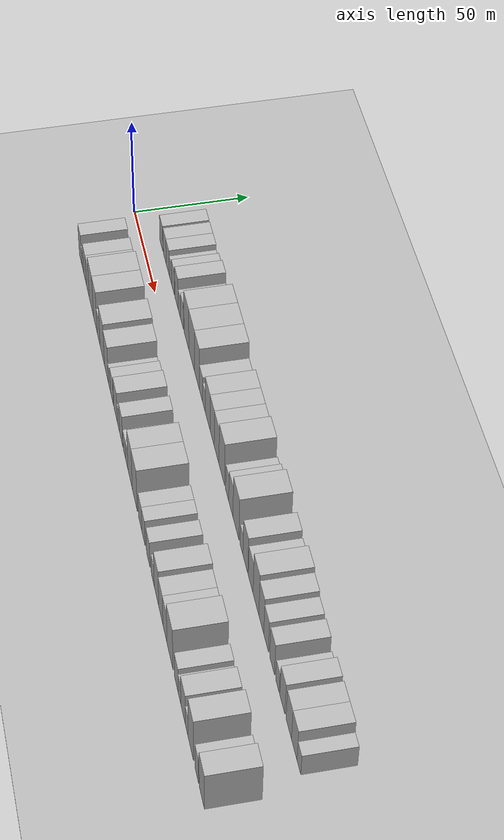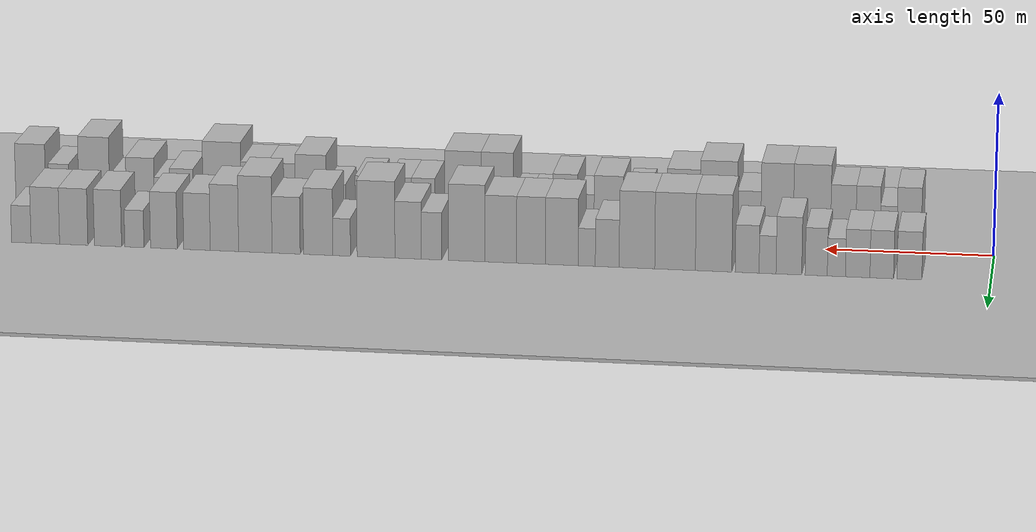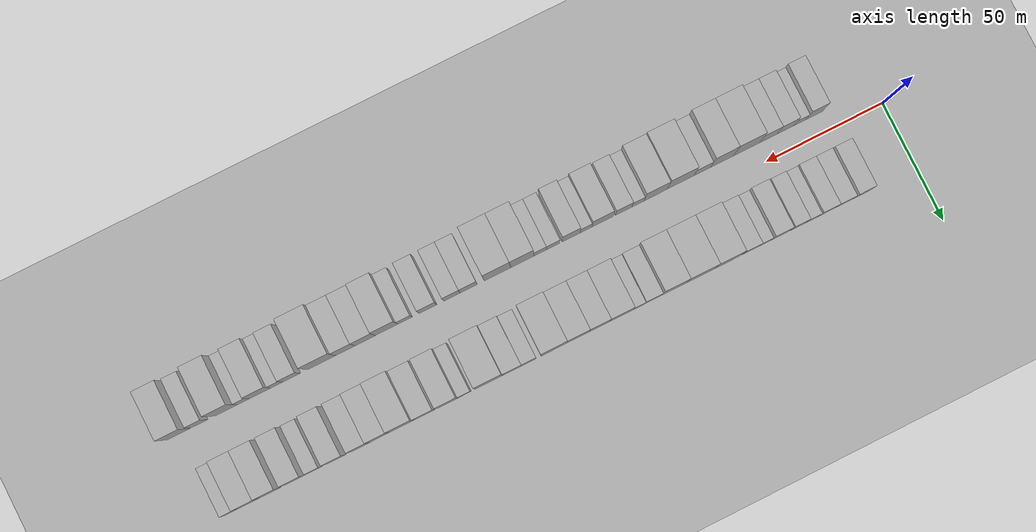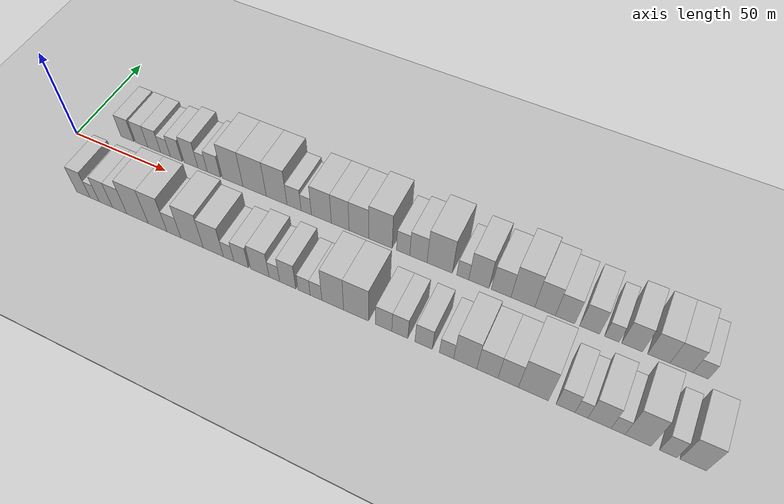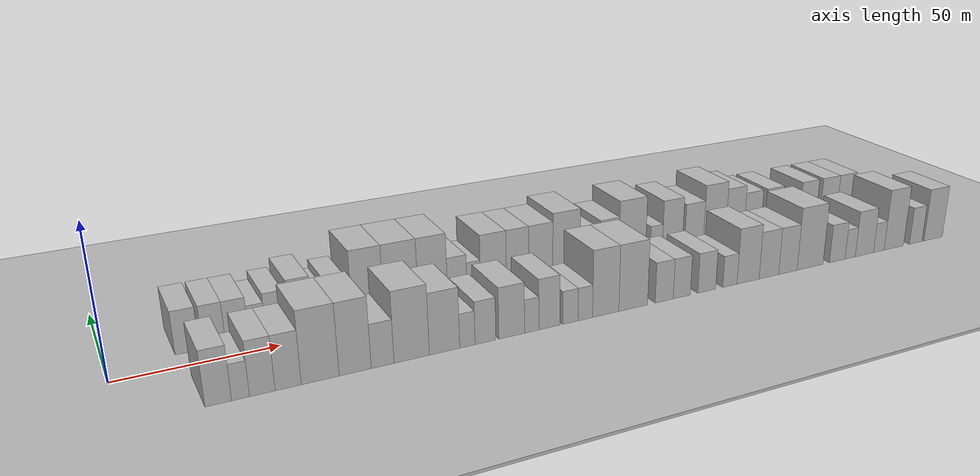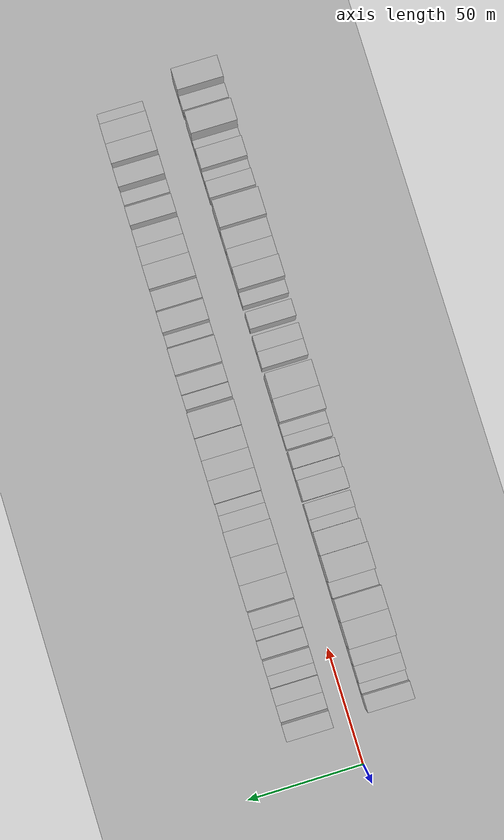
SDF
<?xml version="1.0" encoding="utf-8"?>

<sdf version="1.6">

   <world name="default">

      <gui fullscreen="0">

         <camera name="user_camera">

            <pose>-15 0 4.57585 0 0 0</pose>

            <view_controller>orbit</view_controller>

         </camera>

      </gui>

      <scene>

         <sky>

           <clouds>

             <speed>12</speed>

           </clouds>

         </sky>

         <ambient>0.4 0.4 0.4 1</ambient>

         <background>0.7 0.7 0.7 1</background>

         <shadows>1</shadows>

      </scene>

      <gravity>0 0 -9.8066</gravity>

      <magnetic_field>6e-06 2.3e-05 -4.2e-05</magnetic_field>

      <physics default="0" name="default_physics" type="ode">

         <ode>

            <solver>

               <type>quick</type>

               <iters>10</iters>

               <sor>1.0</sor>

               <use_dynamic_moi_rescaling>0</use_dynamic_moi_rescaling>

            </solver>

            <constraints>

               <cfm>0</cfm>

               <erp>0.2</erp>

               <contact_max_correcting_vel>100</contact_max_correcting_vel>

               <contact_surface_layer>0.001</contact_surface_layer>

            </constraints>

         </ode>

         <max_step_size>0.004</max_step_size>

         <real_time_factor>1</real_time_factor>

         <real_time_update_rate>250</real_time_update_rate>

      </physics>

      <light name="sun" type="directional">

         <cast_shadows>1</cast_shadows>

         <pose>0 0 10 0 0 0</pose>

         <diffuse>0.8 0.8 0.8 1</diffuse>

         <specular>0.2 0.2 0.2 1</specular>

         <attenuation>

            <range>1000</range>

            <constant>0.9</constant>

            <linear>0.01</linear>

            <quadratic>0.001</quadratic>

         </attenuation>

         <direction>-0.5 0.1 -0.9</direction>

      </light>

      <include>

         <name>ground_plane_1</name>

         <uri>model://HANNAS_ground_plane</uri>

         <pose>0 0 0  0 0 0</pose>

      </include>

      <include>

         <name>ground_plane_2</name>

         <uri>model://HANNAS_ground_plane</uri>

         <pose>100 0 0  0 0 0</pose>

      </include>

      <model name="building_1">

         <static>1</static>

         <pose frame="">23.6077 17.5000 0 0.000000 0.000000 1.570796</pose>

         <link name="link">

            <pose frame="">0 0 7.50 0 0 0</pose>

            <collision name="collision">

               <geometry>

                  <box>

                     <size>20.0000 7.2154 15.0000</size>

                  </box>

               </geometry>

               <max_contacts>10</max_contacts>

               <surface>

                  <contact>

                     <ode/>

                  </contact>

                  <bounce/>

                  <friction>

                     <torsional>

                        <ode/>

                     </torsional>

                     <ode/>

                  </friction>

               </surface>

            </collision>

            <visual name="visual">

               <cast_shadows>0</cast_shadows>

               <geometry>

                  <box>

                     <size>20.0000 7.2154 15.0000</size>

                  </box>

               </geometry>

               <material>

                  <script>

                     <uri>model://HANNAS_wall/materials/scripts</uri>

                     <uri>model://HANNAS_wall/materials/textures</uri>

                     <name>vrc/HANNAS_wall</name>

                  </script>

               </material>

            </visual>

            <self_collide>0</self_collide>

            <enable_wind>0</enable_wind>

            <kinematic>0</kinematic>

         </link>

      </model>

      <model name="building_2">

         <static>1</static>

         <pose frame="">31.6629 17.5000 0 0.000000 0.000000 1.570796</pose>

         <link name="link">

            <pose frame="">0 0 7.50 0 0 0</pose>

            <collision name="collision">

               <geometry>

                  <box>

                     <size>20.0000 6.8950 15.0000</size>

                  </box>

               </geometry>

               <max_contacts>10</max_contacts>

               <surface>

                  <contact>

                     <ode/>

                  </contact>

                  <bounce/>

                  <friction>

                     <torsional>

                        <ode/>

                     </torsional>

                     <ode/>

                  </friction>

               </surface>

            </collision>

            <visual name="visual">

               <cast_shadows>0</cast_shadows>

               <geometry>

                  <box>

                     <size>20.0000 6.8950 15.0000</size>

                  </box>

               </geometry>

               <material>

                  <script>

                     <uri>model://HANNAS_wall/materials/scripts</uri>

                     <uri>model://HANNAS_wall/materials/textures</uri>

                     <name>vrc/HANNAS_wall</name>

                  </script>

               </material>

            </visual>

            <self_collide>0</self_collide>

            <enable_wind>0</enable_wind>

            <kinematic>0</kinematic>

         </link>

      </model>

      <model name="building_3">

         <static>1</static>

         <pose frame="">38.6754 17.5000 0 0.000000 0.000000 1.570796</pose>

         <link name="link">

            <pose frame="">0 0 7.50 0 0 0</pose>

            <collision name="collision">

               <geometry>

                  <box>

                     <size>20.0000 7.1300 15.0000</size>

                  </box>

               </geometry>

               <max_contacts>10</max_contacts>

               <surface>

                  <contact>

                     <ode/>

                  </contact>

                  <bounce/>

                  <friction>

                     <torsional>

                        <ode/>

                     </torsional>

                     <ode/>

                  </friction>

               </surface>

            </collision>

            <visual name="visual">

               <cast_shadows>0</cast_shadows>

               <geometry>

                  <box>

                     <size>20.0000 7.1300 15.0000</size>

                  </box>

               </geometry>

               <material>

                  <script>

                     <uri>model://HANNAS_wall/materials/scripts</uri>

                     <uri>model://HANNAS_wall/materials/textures</uri>

                     <name>vrc/HANNAS_wall</name>

                  </script>

               </material>

            </visual>

            <self_collide>0</self_collide>

            <enable_wind>0</enable_wind>

            <kinematic>0</kinematic>

         </link>

      </model>

      <model name="building_4">

         <static>1</static>

         <pose frame="">44.9000 17.5000 0 0.000000 0.000000 1.570796</pose>

         <link name="link">

            <pose frame="">0 0 6.00 0 0 0</pose>

            <collision name="collision">

               <geometry>

                  <box>

                     <size>20.0000 5.3193 12.0000</size>

                  </box>

               </geometry>

               <max_contacts>10</max_contacts>

               <surface>

                  <contact>

                     <ode/>

                  </contact>

                  <bounce/>

                  <friction>

                     <torsional>

                        <ode/>

                     </torsional>

                     <ode/>

                  </friction>

               </surface>

            </collision>

            <visual name="visual">

               <cast_shadows>0</cast_shadows>

               <geometry>

                  <box>

                     <size>20.0000 5.3193 12.0000</size>

                  </box>

               </geometry>

               <material>

                  <script>

                     <uri>model://HANNAS_wall/materials/scripts</uri>

                     <uri>model://HANNAS_wall/materials/textures</uri>

                     <name>vrc/HANNAS_wall</name>

                  </script>

               </material>

            </visual>

            <self_collide>0</self_collide>

            <enable_wind>0</enable_wind>

            <kinematic>0</kinematic>

         </link>

      </model>

      <model name="building_5">

         <static>1</static>

         <pose frame="">50.7931 17.5000 0 0.000000 0.000000 1.570796</pose>

         <link name="link">

            <pose frame="">0 0 7.50 0 0 0</pose>

            <collision name="collision">

               <geometry>

                  <box>

                     <size>20.0000 6.4668 15.0000</size>

                  </box>

               </geometry>

               <max_contacts>10</max_contacts>

               <surface>

                  <contact>

                     <ode/>

                  </contact>

                  <bounce/>

                  <friction>

                     <torsional>

                        <ode/>

                     </torsional>

                     <ode/>

                  </friction>

               </surface>

            </collision>

            <visual name="visual">

               <cast_shadows>0</cast_shadows>

               <geometry>

                  <box>

                     <size>20.0000 6.4668 15.0000</size>

                  </box>

               </geometry>

               <material>

                  <script>

                     <uri>model://HANNAS_wall/materials/scripts</uri>

                     <uri>model://HANNAS_wall/materials/textures</uri>

                     <name>vrc/HANNAS_wall</name>

                  </script>

               </material>

            </visual>

            <self_collide>0</self_collide>

            <enable_wind>0</enable_wind>

            <kinematic>0</kinematic>

         </link>

      </model>

      <model name="building_6">

         <static>1</static>

         <pose frame="">58.7857 17.5000 0 0.000000 0.000000 1.570796</pose>

         <link name="link">

            <pose frame="">0 0 9.00 0 0 0</pose>

            <collision name="collision">

               <geometry>

                  <box>

                     <size>20.0000 7.5184 18.0000</size>

                  </box>

               </geometry>

               <max_contacts>10</max_contacts>

               <surface>

                  <contact>

                     <ode/>

                  </contact>

                  <bounce/>

                  <friction>

                     <torsional>

                        <ode/>

                     </torsional>

                     <ode/>

                  </friction>

               </surface>

            </collision>

            <visual name="visual">

               <cast_shadows>0</cast_shadows>

               <geometry>

                  <box>

                     <size>20.0000 7.5184 18.0000</size>

                  </box>

               </geometry>

               <material>

                  <script>

                     <uri>model://HANNAS_wall/materials/scripts</uri>

                     <uri>model://HANNAS_wall/materials/textures</uri>

                     <name>vrc/HANNAS_wall</name>

                  </script>

               </material>

            </visual>

            <self_collide>0</self_collide>

            <enable_wind>0</enable_wind>

            <kinematic>0</kinematic>

         </link>

      </model>

      <model name="building_7">

         <static>1</static>

         <pose frame="">65.0388 17.5000 0 0.000000 0.000000 1.570796</pose>

         <link name="link">

            <pose frame="">0 0 6.00 0 0 0</pose>

            <collision name="collision">

               <geometry>

                  <box>

                     <size>20.0000 4.9879 12.0000</size>

                  </box>

               </geometry>

               <max_contacts>10</max_contacts>

               <surface>

                  <contact>

                     <ode/>

                  </contact>

                  <bounce/>

                  <friction>

                     <torsional>

                        <ode/>

                     </torsional>

                     <ode/>

                  </friction>

               </surface>

            </collision>

            <visual name="visual">

               <cast_shadows>0</cast_shadows>

               <geometry>

                  <box>

                     <size>20.0000 4.9879 12.0000</size>

                  </box>

               </geometry>

               <material>

                  <script>

                     <uri>model://HANNAS_wall/materials/scripts</uri>

                     <uri>model://HANNAS_wall/materials/textures</uri>

                     <name>vrc/HANNAS_wall</name>

                  </script>

               </material>

            </visual>

            <self_collide>0</self_collide>

            <enable_wind>0</enable_wind>

            <kinematic>0</kinematic>

         </link>

      </model>

      <model name="building_8">

         <static>1</static>

         <pose frame="">71.0306 17.5000 0 0.000000 0.000000 1.570796</pose>

         <link name="link">

            <pose frame="">0 0 7.50 0 0 0</pose>

            <collision name="collision">

               <geometry>

                  <box>

                     <size>20.0000 6.9957 15.0000</size>

                  </box>

               </geometry>

               <max_contacts>10</max_contacts>

               <surface>

                  <contact>

                     <ode/>

                  </contact>

                  <bounce/>

                  <friction>

                     <torsional>

                        <ode/>

                     </torsional>

                     <ode/>

                  </friction>

               </surface>

            </collision>

            <visual name="visual">

               <cast_shadows>0</cast_shadows>

               <geometry>

                  <box>

                     <size>20.0000 6.9957 15.0000</size>

                  </box>

               </geometry>

               <material>

                  <script>

                     <uri>model://HANNAS_wall/materials/scripts</uri>

                     <uri>model://HANNAS_wall/materials/textures</uri>

                     <name>vrc/HANNAS_wall</name>

                  </script>

               </material>

            </visual>

            <self_collide>0</self_collide>

            <enable_wind>0</enable_wind>

            <kinematic>0</kinematic>

         </link>

      </model>

      <model name="building_9">

         <static>1</static>

         <pose frame="">80.8923 17.5000 0 0.000000 0.000000 1.570796</pose>

         <link name="link">

            <pose frame="">0 0 12.00 0 0 0</pose>

            <collision name="collision">

               <geometry>

                  <box>

                     <size>20.0000 10.7277 24.0000</size>

                  </box>

               </geometry>

               <max_contacts>10</max_contacts>

               <surface>

                  <contact>

                     <ode/>

                  </contact>

                  <bounce/>

                  <friction>

                     <torsional>

                        <ode/>

                     </torsional>

                     <ode/>

                  </friction>

               </surface>

            </collision>

            <visual name="visual">

               <cast_shadows>0</cast_shadows>

               <geometry>

                  <box>

                     <size>20.0000 10.7277 24.0000</size>

                  </box>

               </geometry>

               <material>

                  <script>

                     <uri>model://HANNAS_wall/materials/scripts</uri>

                     <uri>model://HANNAS_wall/materials/textures</uri>

                     <name>vrc/HANNAS_wall</name>

                  </script>

               </material>

            </visual>

            <self_collide>0</self_collide>

            <enable_wind>0</enable_wind>

            <kinematic>0</kinematic>

         </link>

      </model>

      <model name="building_10">

         <static>1</static>

         <pose frame="">92.2401 17.5000 0 0.000000 0.000000 1.570796</pose>

         <link name="link">

            <pose frame="">0 0 12.00 0 0 0</pose>

            <collision name="collision">

               <geometry>

                  <box>

                     <size>20.0000 11.9680 24.0000</size>

                  </box>

               </geometry>

               <max_contacts>10</max_contacts>

               <surface>

                  <contact>

                     <ode/>

                  </contact>

                  <bounce/>

                  <friction>

                     <torsional>

                        <ode/>

                     </torsional>

                     <ode/>

                  </friction>

               </surface>

            </collision>

            <visual name="visual">

               <cast_shadows>0</cast_shadows>

               <geometry>

                  <box>

                     <size>20.0000 11.9680 24.0000</size>

                  </box>

               </geometry>

               <material>

                  <script>

                     <uri>model://HANNAS_wall/materials/scripts</uri>

                     <uri>model://HANNAS_wall/materials/textures</uri>

                     <name>vrc/HANNAS_wall</name>

                  </script>

               </material>

            </visual>

            <self_collide>0</self_collide>

            <enable_wind>0</enable_wind>

            <kinematic>0</kinematic>

         </link>

      </model>

      <model name="building_11">

         <static>1</static>

         <pose frame="">103.4802 17.5000 0 0.000000 0.000000 1.570796</pose>

         <link name="link">

            <pose frame="">0 0 12.00 0 0 0</pose>

            <collision name="collision">

               <geometry>

                  <box>

                     <size>20.0000 10.5121 24.0000</size>

                  </box>

               </geometry>

               <max_contacts>10</max_contacts>

               <surface>

                  <contact>

                     <ode/>

                  </contact>

                  <bounce/>

                  <friction>

                     <torsional>

                        <ode/>

                     </torsional>

                     <ode/>

                  </friction>

               </surface>

            </collision>

            <visual name="visual">

               <cast_shadows>0</cast_shadows>

               <geometry>

                  <box>

                     <size>20.0000 10.5121 24.0000</size>

                  </box>

               </geometry>

               <material>

                  <script>

                     <uri>model://HANNAS_wall/materials/scripts</uri>

                     <uri>model://HANNAS_wall/materials/textures</uri>

                     <name>vrc/HANNAS_wall</name>

                  </script>

               </material>

            </visual>

            <self_collide>0</self_collide>

            <enable_wind>0</enable_wind>

            <kinematic>0</kinematic>

         </link>

      </model>

      <model name="building_12">

         <static>1</static>

         <pose frame="">112.2710 17.5000 0 0.000000 0.000000 1.570796</pose>

         <link name="link">

            <pose frame="">0 0 7.50 0 0 0</pose>

            <collision name="collision">

               <geometry>

                  <box>

                     <size>20.0000 7.0695 15.0000</size>

                  </box>

               </geometry>

               <max_contacts>10</max_contacts>

               <surface>

                  <contact>

                     <ode/>

                  </contact>

                  <bounce/>

                  <friction>

                     <torsional>

                        <ode/>

                     </torsional>

                     <ode/>

                  </friction>

               </surface>

            </collision>

            <visual name="visual">

               <cast_shadows>0</cast_shadows>

               <geometry>

                  <box>

                     <size>20.0000 7.0695 15.0000</size>

                  </box>

               </geometry>

               <material>

                  <script>

                     <uri>model://HANNAS_wall/materials/scripts</uri>

                     <uri>model://HANNAS_wall/materials/textures</uri>

                     <name>vrc/HANNAS_wall</name>

                  </script>

               </material>

            </visual>

            <self_collide>0</self_collide>

            <enable_wind>0</enable_wind>

            <kinematic>0</kinematic>

         </link>

      </model>

      <model name="building_13">

         <static>1</static>

         <pose frame="">118.3395 17.5000 0 0.000000 0.000000 1.570796</pose>

         <link name="link">

            <pose frame="">0 0 6.00 0 0 0</pose>

            <collision name="collision">

               <geometry>

                  <box>

                     <size>20.0000 5.0676 12.0000</size>

                  </box>

               </geometry>

               <max_contacts>10</max_contacts>

               <surface>

                  <contact>

                     <ode/>

                  </contact>

                  <bounce/>

                  <friction>

                     <torsional>

                        <ode/>

                     </torsional>

                     <ode/>

                  </friction>

               </surface>

            </collision>

            <visual name="visual">

               <cast_shadows>0</cast_shadows>

               <geometry>

                  <box>

                     <size>20.0000 5.0676 12.0000</size>

                  </box>

               </geometry>

               <material>

                  <script>

                     <uri>model://HANNAS_wall/materials/scripts</uri>

                     <uri>model://HANNAS_wall/materials/textures</uri>

                     <name>vrc/HANNAS_wall</name>

                  </script>

               </material>

            </visual>

            <self_collide>0</self_collide>

            <enable_wind>0</enable_wind>

            <kinematic>0</kinematic>

         </link>

      </model>

      <model name="building_14">

         <static>1</static>

         <pose frame="">125.7330 17.5000 0 0.000000 0.000000 1.570796</pose>

         <link name="link">

            <pose frame="">0 0 10.50 0 0 0</pose>

            <collision name="collision">

               <geometry>

                  <box>

                     <size>20.0000 9.7193 21.0000</size>

                  </box>

               </geometry>

               <max_contacts>10</max_contacts>

               <surface>

                  <contact>

                     <ode/>

                  </contact>

                  <bounce/>

                  <friction>

                     <torsional>

                        <ode/>

                     </torsional>

                     <ode/>

                  </friction>

               </surface>

            </collision>

            <visual name="visual">

               <cast_shadows>0</cast_shadows>

               <geometry>

                  <box>

                     <size>20.0000 9.7193 21.0000</size>

                  </box>

               </geometry>

               <material>

                  <script>

                     <uri>model://HANNAS_wall/materials/scripts</uri>

                     <uri>model://HANNAS_wall/materials/textures</uri>

                     <name>vrc/HANNAS_wall</name>

                  </script>

               </material>

            </visual>

            <self_collide>0</self_collide>

            <enable_wind>0</enable_wind>

            <kinematic>0</kinematic>

         </link>

      </model>

      <model name="building_15">

         <static>1</static>

         <pose frame="">134.8650 17.5000 0 0.000000 0.000000 1.570796</pose>

         <link name="link">

            <pose frame="">0 0 10.50 0 0 0</pose>

            <collision name="collision">

               <geometry>

                  <box>

                     <size>20.0000 8.5447 21.0000</size>

                  </box>

               </geometry>

               <max_contacts>10</max_contacts>

               <surface>

                  <contact>

                     <ode/>

                  </contact>

                  <bounce/>

                  <friction>

                     <torsional>

                        <ode/>

                     </torsional>

                     <ode/>

                  </friction>

               </surface>

            </collision>

            <visual name="visual">

               <cast_shadows>0</cast_shadows>

               <geometry>

                  <box>

                     <size>20.0000 8.5447 21.0000</size>

                  </box>

               </geometry>

               <material>

                  <script>

                     <uri>model://HANNAS_wall/materials/scripts</uri>

                     <uri>model://HANNAS_wall/materials/textures</uri>

                     <name>vrc/HANNAS_wall</name>

                  </script>

               </material>

            </visual>

            <self_collide>0</self_collide>

            <enable_wind>0</enable_wind>

            <kinematic>0</kinematic>

         </link>

      </model>

      <model name="building_16">

         <static>1</static>

         <pose frame="">143.8493 17.5000 0 0.000000 0.000000 1.570796</pose>

         <link name="link">

            <pose frame="">0 0 10.50 0 0 0</pose>

            <collision name="collision">

               <geometry>

                  <box>

                     <size>20.0000 9.4239 21.0000</size>

                  </box>

               </geometry>

               <max_contacts>10</max_contacts>

               <surface>

                  <contact>

                     <ode/>

                  </contact>

                  <bounce/>

                  <friction>

                     <torsional>

                        <ode/>

                     </torsional>

                     <ode/>

                  </friction>

               </surface>

            </collision>

            <visual name="visual">

               <cast_shadows>0</cast_shadows>

               <geometry>

                  <box>

                     <size>20.0000 9.4239 21.0000</size>

                  </box>

               </geometry>

               <material>

                  <script>

                     <uri>model://HANNAS_wall/materials/scripts</uri>

                     <uri>model://HANNAS_wall/materials/textures</uri>

                     <name>vrc/HANNAS_wall</name>

                  </script>

               </material>

            </visual>

            <self_collide>0</self_collide>

            <enable_wind>0</enable_wind>

            <kinematic>0</kinematic>

         </link>

      </model>

      <model name="building_17">

         <static>1</static>

         <pose frame="">154.0123 17.5000 0 0.000000 0.000000 1.570796</pose>

         <link name="link">

            <pose frame="">0 0 12.00 0 0 0</pose>

            <collision name="collision">

               <geometry>

                  <box>

                     <size>20.0000 10.9021 24.0000</size>

                  </box>

               </geometry>

               <max_contacts>10</max_contacts>

               <surface>

                  <contact>

                     <ode/>

                  </contact>

                  <bounce/>

                  <friction>

                     <torsional>

                        <ode/>

                     </torsional>

                     <ode/>

                  </friction>

               </surface>

            </collision>

            <visual name="visual">

               <cast_shadows>0</cast_shadows>

               <geometry>

                  <box>

                     <size>20.0000 10.9021 24.0000</size>

                  </box>

               </geometry>

               <material>

                  <script>

                     <uri>model://HANNAS_wall/materials/scripts</uri>

                     <uri>model://HANNAS_wall/materials/textures</uri>

                     <name>vrc/HANNAS_wall</name>

                  </script>

               </material>

            </visual>

            <self_collide>0</self_collide>

            <enable_wind>0</enable_wind>

            <kinematic>0</kinematic>

         </link>

      </model>

      <model name="building_18">

         <static>1</static>

         <pose frame="">164.5241 17.5000 0 0.000000 0.000000 1.570796</pose>

         <link name="link">

            <pose frame="">0 0 7.50 0 0 0</pose>

            <collision name="collision">

               <geometry>

                  <box>

                     <size>20.0000 6.1215 15.0000</size>

                  </box>

               </geometry>

               <max_contacts>10</max_contacts>

               <surface>

                  <contact>

                     <ode/>

                  </contact>

                  <bounce/>

                  <friction>

                     <torsional>

                        <ode/>

                     </torsional>

                     <ode/>

                  </friction>

               </surface>

            </collision>

            <visual name="visual">

               <cast_shadows>0</cast_shadows>

               <geometry>

                  <box>

                     <size>20.0000 6.1215 15.0000</size>

                  </box>

               </geometry>

               <material>

                  <script>

                     <uri>model://HANNAS_wall/materials/scripts</uri>

                     <uri>model://HANNAS_wall/materials/textures</uri>

                     <name>vrc/HANNAS_wall</name>

                  </script>

               </material>

            </visual>

            <self_collide>0</self_collide>

            <enable_wind>0</enable_wind>

            <kinematic>0</kinematic>

         </link>

      </model>

      <model name="building_19">

         <static>1</static>

         <pose frame="">171.5248 17.5000 0 0.000000 0.000000 1.570796</pose>

         <link name="link">

            <pose frame="">0 0 9.00 0 0 0</pose>

            <collision name="collision">

               <geometry>

                  <box>

                     <size>20.0000 7.8799 18.0000</size>

                  </box>

               </geometry>

               <max_contacts>10</max_contacts>

               <surface>

                  <contact>

                     <ode/>

                  </contact>

                  <bounce/>

                  <friction>

                     <torsional>

                        <ode/>

                     </torsional>

                     <ode/>

                  </friction>

               </surface>

            </collision>

            <visual name="visual">

               <cast_shadows>0</cast_shadows>

               <geometry>

                  <box>

                     <size>20.0000 7.8799 18.0000</size>

                  </box>

               </geometry>

               <material>

                  <script>

                     <uri>model://HANNAS_wall/materials/scripts</uri>

                     <uri>model://HANNAS_wall/materials/textures</uri>

                     <name>vrc/HANNAS_wall</name>

                  </script>

               </material>

            </visual>

            <self_collide>0</self_collide>

            <enable_wind>0</enable_wind>

            <kinematic>0</kinematic>

         </link>

      </model>

      <model name="building_20">

         <static>1</static>

         <pose frame="">181.1410 17.5000 0 0.000000 0.000000 1.570796</pose>

         <link name="link">

            <pose frame="">0 0 12.00 0 0 0</pose>

            <collision name="collision">

               <geometry>

                  <box>

                     <size>20.0000 11.3526 24.0000</size>

                  </box>

               </geometry>

               <max_contacts>10</max_contacts>

               <surface>

                  <contact>

                     <ode/>

                  </contact>

                  <bounce/>

                  <friction>

                     <torsional>

                        <ode/>

                     </torsional>

                     <ode/>

                  </friction>

               </surface>

            </collision>

            <visual name="visual">

               <cast_shadows>0</cast_shadows>

               <geometry>

                  <box>

                     <size>20.0000 11.3526 24.0000</size>

                  </box>

               </geometry>

               <material>

                  <script>

                     <uri>model://HANNAS_wall/materials/scripts</uri>

                     <uri>model://HANNAS_wall/materials/textures</uri>

                     <name>vrc/HANNAS_wall</name>

                  </script>

               </material>

            </visual>

            <self_collide>0</self_collide>

            <enable_wind>0</enable_wind>

            <kinematic>0</kinematic>

         </link>

      </model>

      <model name="building_21">

         <static>1</static>

         <pose frame="">191.4542 17.5000 0 0.000000 0.000000 1.570796</pose>

         <link name="link">

            <pose frame="">0 0 6.00 0 0 0</pose>

            <collision name="collision">

               <geometry>

                  <box>

                     <size>20.0000 5.2737 12.0000</size>

                  </box>

               </geometry>

               <max_contacts>10</max_contacts>

               <surface>

                  <contact>

                     <ode/>

                  </contact>

                  <bounce/>

                  <friction>

                     <torsional>

                        <ode/>

                     </torsional>

                     <ode/>

                  </friction>

               </surface>

            </collision>

            <visual name="visual">

               <cast_shadows>0</cast_shadows>

               <geometry>

                  <box>

                     <size>20.0000 5.2737 12.0000</size>

                  </box>

               </geometry>

               <material>

                  <script>

                     <uri>model://HANNAS_wall/materials/scripts</uri>

                     <uri>model://HANNAS_wall/materials/textures</uri>

                     <name>vrc/HANNAS_wall</name>

                  </script>

               </material>

            </visual>

            <self_collide>0</self_collide>

            <enable_wind>0</enable_wind>

            <kinematic>0</kinematic>

         </link>

      </model>

      <model name="building_22">

         <static>1</static>

         <pose frame="">198.5105 17.5000 0 0.000000 0.000000 1.570796</pose>

         <link name="link">

            <pose frame="">0 0 10.50 0 0 0</pose>

            <collision name="collision">

               <geometry>

                  <box>

                     <size>20.0000 8.8389 21.0000</size>

                  </box>

               </geometry>

               <max_contacts>10</max_contacts>

               <surface>

                  <contact>

                     <ode/>

                  </contact>

                  <bounce/>

                  <friction>

                     <torsional>

                        <ode/>

                     </torsional>

                     <ode/>

                  </friction>

               </surface>

            </collision>

            <visual name="visual">

               <cast_shadows>0</cast_shadows>

               <geometry>

                  <box>

                     <size>20.0000 8.8389 21.0000</size>

                  </box>

               </geometry>

               <material>

                  <script>

                     <uri>model://HANNAS_wall/materials/scripts</uri>

                     <uri>model://HANNAS_wall/materials/textures</uri>

                     <name>vrc/HANNAS_wall</name>

                  </script>

               </material>

            </visual>

            <self_collide>0</self_collide>

            <enable_wind>0</enable_wind>

            <kinematic>0</kinematic>

         </link>

      </model>

      <model name="building_23">

         <static>1</static>

         <pose frame="">208.1650 17.5000 0 0.000000 0.000000 1.570796</pose>

         <link name="link">

            <pose frame="">0 0 9.00 0 0 0</pose>

            <collision name="collision">

               <geometry>

                  <box>

                     <size>20.0000 8.4702 18.0000</size>

                  </box>

               </geometry>

               <max_contacts>10</max_contacts>

               <surface>

                  <contact>

                     <ode/>

                  </contact>

                  <bounce/>

                  <friction>

                     <torsional>

                        <ode/>

                     </torsional>

                     <ode/>

                  </friction>

               </surface>

            </collision>

            <visual name="visual">

               <cast_shadows>0</cast_shadows>

               <geometry>

                  <box>

                     <size>20.0000 8.4702 18.0000</size>

                  </box>

               </geometry>

               <material>

                  <script>

                     <uri>model://HANNAS_wall/materials/scripts</uri>

                     <uri>model://HANNAS_wall/materials/textures</uri>

                     <name>vrc/HANNAS_wall</name>

                  </script>

               </material>

            </visual>

            <self_collide>0</self_collide>

            <enable_wind>0</enable_wind>

            <kinematic>0</kinematic>

         </link>

      </model>

      <model name="building_24">

         <static>1</static>

         <pose frame="">217.4503 17.5000 0 0.000000 0.000000 1.570796</pose>

         <link name="link">

            <pose frame="">0 0 12.00 0 0 0</pose>

            <collision name="collision">

               <geometry>

                  <box>

                     <size>20.0000 10.1003 24.0000</size>

                  </box>

               </geometry>

               <max_contacts>10</max_contacts>

               <surface>

                  <contact>

                     <ode/>

                  </contact>

                  <bounce/>

                  <friction>

                     <torsional>

                        <ode/>

                     </torsional>

                     <ode/>

                  </friction>

               </surface>

            </collision>

            <visual name="visual">

               <cast_shadows>0</cast_shadows>

               <geometry>

                  <box>

                     <size>20.0000 10.1003 24.0000</size>

                  </box>

               </geometry>

               <material>

                  <script>

                     <uri>model://HANNAS_wall/materials/scripts</uri>

                     <uri>model://HANNAS_wall/materials/textures</uri>

                     <name>vrc/HANNAS_wall</name>

                  </script>

               </material>

            </visual>

            <self_collide>0</self_collide>

            <enable_wind>0</enable_wind>

            <kinematic>0</kinematic>

         </link>

      </model>

      <model name="building_25">

         <static>1</static>

         <pose frame="">226.7920 17.5000 0 0.000000 0.000000 1.570796</pose>

         <link name="link">

            <pose frame="">0 0 10.50 0 0 0</pose>

            <collision name="collision">

               <geometry>

                  <box>

                     <size>20.0000 8.5831 21.0000</size>

                  </box>

               </geometry>

               <max_contacts>10</max_contacts>

               <surface>

                  <contact>

                     <ode/>

                  </contact>

                  <bounce/>

                  <friction>

                     <torsional>

                        <ode/>

                     </torsional>

                     <ode/>

                  </friction>

               </surface>

            </collision>

            <visual name="visual">

               <cast_shadows>0</cast_shadows>

               <geometry>

                  <box>

                     <size>20.0000 8.5831 21.0000</size>

                  </box>

               </geometry>

               <material>

                  <script>

                     <uri>model://HANNAS_wall/materials/scripts</uri>

                     <uri>model://HANNAS_wall/materials/textures</uri>

                     <name>vrc/HANNAS_wall</name>

                  </script>

               </material>

            </visual>

            <self_collide>0</self_collide>

            <enable_wind>0</enable_wind>

            <kinematic>0</kinematic>

         </link>

      </model>

      <model name="building_26">

         <static>1</static>

         <pose frame="">235.0983 17.5000 0 0.000000 0.000000 1.570796</pose>

         <link name="link">

            <pose frame="">0 0 9.00 0 0 0</pose>

            <collision name="collision">

               <geometry>

                  <box>

                     <size>20.0000 8.0295 18.0000</size>

                  </box>

               </geometry>

               <max_contacts>10</max_contacts>

               <surface>

                  <contact>

                     <ode/>

                  </contact>

                  <bounce/>

                  <friction>

                     <torsional>

                        <ode/>

                     </torsional>

                     <ode/>

                  </friction>

               </surface>

            </collision>

            <visual name="visual">

               <cast_shadows>0</cast_shadows>

               <geometry>

                  <box>

                     <size>20.0000 8.0295 18.0000</size>

                  </box>

               </geometry>

               <material>

                  <script>

                     <uri>model://HANNAS_wall/materials/scripts</uri>

                     <uri>model://HANNAS_wall/materials/textures</uri>

                     <name>vrc/HANNAS_wall</name>

                  </script>

               </material>

            </visual>

            <self_collide>0</self_collide>

            <enable_wind>0</enable_wind>

            <kinematic>0</kinematic>

         </link>

      </model>

      <model name="building_27">

         <static>1</static>

         <pose frame="">245.1571 17.5000 0 0.000000 0.000000 1.570796</pose>

         <link name="link">

            <pose frame="">0 0 9.00 0 0 0</pose>

            <collision name="collision">

               <geometry>

                  <box>

                     <size>20.0000 8.0883 18.0000</size>

                  </box>

               </geometry>

               <max_contacts>10</max_contacts>

               <surface>

                  <contact>

                     <ode/>

                  </contact>

                  <bounce/>

                  <friction>

                     <torsional>

                        <ode/>

                     </torsional>

                     <ode/>

                  </friction>

               </surface>

            </collision>

            <visual name="visual">

               <cast_shadows>0</cast_shadows>

               <geometry>

                  <box>

                     <size>20.0000 8.0883 18.0000</size>

                  </box>

               </geometry>

               <material>

                  <script>

                     <uri>model://HANNAS_wall/materials/scripts</uri>

                     <uri>model://HANNAS_wall/materials/textures</uri>

                     <name>vrc/HANNAS_wall</name>

                  </script>

               </material>

            </visual>

            <self_collide>0</self_collide>

            <enable_wind>0</enable_wind>

            <kinematic>0</kinematic>

         </link>

      </model>

      <model name="building_28">

         <static>1</static>

         <pose frame="">254.1018 17.5000 0 0.000000 0.000000 1.570796</pose>

         <link name="link">

            <pose frame="">0 0 6.00 0 0 0</pose>

            <collision name="collision">

               <geometry>

                  <box>

                     <size>20.0000 5.8010 12.0000</size>

                  </box>

               </geometry>

               <max_contacts>10</max_contacts>

               <surface>

                  <contact>

                     <ode/>

                  </contact>

                  <bounce/>

                  <friction>

                     <torsional>

                        <ode/>

                     </torsional>

                     <ode/>

                  </friction>

               </surface>

            </collision>

            <visual name="visual">

               <cast_shadows>0</cast_shadows>

               <geometry>

                  <box>

                     <size>20.0000 5.8010 12.0000</size>

                  </box>

               </geometry>

               <material>

                  <script>

                     <uri>model://HANNAS_wall/materials/scripts</uri>

                     <uri>model://HANNAS_wall/materials/textures</uri>

                     <name>vrc/HANNAS_wall</name>

                  </script>

               </material>

            </visual>

            <self_collide>0</self_collide>

            <enable_wind>0</enable_wind>

            <kinematic>0</kinematic>

         </link>

      </model>

      <model name="building_29">

         <static>1</static>

         <pose frame="">262.1307 17.5000 0 0.000000 0.000000 1.570796</pose>

         <link name="link">

            <pose frame="">0 0 9.00 0 0 0</pose>

            <collision name="collision">

               <geometry>

                  <box>

                     <size>20.0000 8.2567 18.0000</size>

                  </box>

               </geometry>

               <max_contacts>10</max_contacts>

               <surface>

                  <contact>

                     <ode/>

                  </contact>

                  <bounce/>

                  <friction>

                     <torsional>

                        <ode/>

                     </torsional>

                     <ode/>

                  </friction>

               </surface>

            </collision>

            <visual name="visual">

               <cast_shadows>0</cast_shadows>

               <geometry>

                  <box>

                     <size>20.0000 8.2567 18.0000</size>

                  </box>

               </geometry>

               <material>

                  <script>

                     <uri>model://HANNAS_wall/materials/scripts</uri>

                     <uri>model://HANNAS_wall/materials/textures</uri>

                     <name>vrc/HANNAS_wall</name>

                  </script>

               </material>

            </visual>

            <self_collide>0</self_collide>

            <enable_wind>0</enable_wind>

            <kinematic>0</kinematic>

         </link>

      </model>

      <model name="building_30">

         <static>1</static>

         <pose frame="">272.5766 17.5000 0 0.000000 0.000000 1.570796</pose>

         <link name="link">

            <pose frame="">0 0 9.00 0 0 0</pose>

            <collision name="collision">

               <geometry>

                  <box>

                     <size>20.0000 8.6352 18.0000</size>

                  </box>

               </geometry>

               <max_contacts>10</max_contacts>

               <surface>

                  <contact>

                     <ode/>

                  </contact>

                  <bounce/>

                  <friction>

                     <torsional>

                        <ode/>

                     </torsional>

                     <ode/>

                  </friction>

               </surface>

            </collision>

            <visual name="visual">

               <cast_shadows>0</cast_shadows>

               <geometry>

                  <box>

                     <size>20.0000 8.6352 18.0000</size>

                  </box>

               </geometry>

               <material>

                  <script>

                     <uri>model://HANNAS_wall/materials/scripts</uri>

                     <uri>model://HANNAS_wall/materials/textures</uri>

                     <name>vrc/HANNAS_wall</name>

                  </script>

               </material>

            </visual>

            <self_collide>0</self_collide>

            <enable_wind>0</enable_wind>

            <kinematic>0</kinematic>

         </link>

      </model>

      <model name="building_31">

         <static>1</static>

         <pose frame="">281.2514 17.5000 0 0.000000 0.000000 1.570796</pose>

         <link name="link">

            <pose frame="">0 0 9.00 0 0 0</pose>

            <collision name="collision">

               <geometry>

                  <box>

                     <size>20.0000 8.7143 18.0000</size>

                  </box>

               </geometry>

               <max_contacts>10</max_contacts>

               <surface>

                  <contact>

                     <ode/>

                  </contact>

                  <bounce/>

                  <friction>

                     <torsional>

                        <ode/>

                     </torsional>

                     <ode/>

                  </friction>

               </surface>

            </collision>

            <visual name="visual">

               <cast_shadows>0</cast_shadows>

               <geometry>

                  <box>

                     <size>20.0000 8.7143 18.0000</size>

                  </box>

               </geometry>

               <material>

                  <script>

                     <uri>model://HANNAS_wall/materials/scripts</uri>

                     <uri>model://HANNAS_wall/materials/textures</uri>

                     <name>vrc/HANNAS_wall</name>

                  </script>

               </material>

            </visual>

            <self_collide>0</self_collide>

            <enable_wind>0</enable_wind>

            <kinematic>0</kinematic>

         </link>

      </model>

      <model name="building_32">

         <static>1</static>

         <pose frame="">288.5877 17.5000 0 0.000000 0.000000 1.570796</pose>

         <link name="link">

            <pose frame="">0 0 6.00 0 0 0</pose>

            <collision name="collision">

               <geometry>

                  <box>

                     <size>20.0000 5.9582 12.0000</size>

                  </box>

               </geometry>

               <max_contacts>10</max_contacts>

               <surface>

                  <contact>

                     <ode/>

                  </contact>

                  <bounce/>

                  <friction>

                     <torsional>

                        <ode/>

                     </torsional>

                     <ode/>

                  </friction>

               </surface>

            </collision>

            <visual name="visual">

               <cast_shadows>0</cast_shadows>

               <geometry>

                  <box>

                     <size>20.0000 5.9582 12.0000</size>

                  </box>

               </geometry>

               <material>

                  <script>

                     <uri>model://HANNAS_wall/materials/scripts</uri>

                     <uri>model://HANNAS_wall/materials/textures</uri>

                     <name>vrc/HANNAS_wall</name>

                  </script>

               </material>

            </visual>

            <self_collide>0</self_collide>

            <enable_wind>0</enable_wind>

            <kinematic>0</kinematic>

         </link>

      </model>

      <model name="building_33">

         <static>1</static>

         <pose frame="">25.6503 -17.5000 0 0.000000 0.000000 1.570796</pose>

         <link name="link">

            <pose frame="">0 0 9.00 0 0 0</pose>

            <collision name="collision">

               <geometry>

                  <box>

                     <size>20.0000 7.3007 18.0000</size>

                  </box>

               </geometry>

               <max_contacts>10</max_contacts>

               <surface>

                  <contact>

                     <ode/>

                  </contact>

                  <bounce/>

                  <friction>

                     <torsional>

                        <ode/>

                     </torsional>

                     <ode/>

                  </friction>

               </surface>

            </collision>

            <visual name="visual">

               <cast_shadows>0</cast_shadows>

               <geometry>

                  <box>

                     <size>20.0000 7.3007 18.0000</size>

                  </box>

               </geometry>

               <material>

                  <script>

                     <uri>model://HANNAS_wall/materials/scripts</uri>

                     <uri>model://HANNAS_wall/materials/textures</uri>

                     <name>vrc/HANNAS_wall</name>

                  </script>

               </material>

            </visual>

            <self_collide>0</self_collide>

            <enable_wind>0</enable_wind>

            <kinematic>0</kinematic>

         </link>

      </model>

      <model name="building_34">

         <static>1</static>

         <pose frame="">31.7926 -17.5000 0 0.000000 0.000000 1.570796</pose>

         <link name="link">

            <pose frame="">0 0 6.00 0 0 0</pose>

            <collision name="collision">

               <geometry>

                  <box>

                     <size>20.0000 4.9839 12.0000</size>

                  </box>

               </geometry>

               <max_contacts>10</max_contacts>

               <surface>

                  <contact>

                     <ode/>

                  </contact>

                  <bounce/>

                  <friction>

                     <torsional>

                        <ode/>

                     </torsional>

                     <ode/>

                  </friction>

               </surface>

            </collision>

            <visual name="visual">

               <cast_shadows>0</cast_shadows>

               <geometry>

                  <box>

                     <size>20.0000 4.9839 12.0000</size>

                  </box>

               </geometry>

               <material>

                  <script>

                     <uri>model://HANNAS_wall/materials/scripts</uri>

                     <uri>model://HANNAS_wall/materials/textures</uri>

                     <name>vrc/HANNAS_wall</name>

                  </script>

               </material>

            </visual>

            <self_collide>0</self_collide>

            <enable_wind>0</enable_wind>

            <kinematic>0</kinematic>

         </link>

      </model>

      <model name="building_35">

         <static>1</static>

         <pose frame="">37.9066 -17.5000 0 0.000000 0.000000 1.570796</pose>

         <link name="link">

            <pose frame="">0 0 9.00 0 0 0</pose>

            <collision name="collision">

               <geometry>

                  <box>

                     <size>20.0000 7.2442 18.0000</size>

                  </box>

               </geometry>

               <max_contacts>10</max_contacts>

               <surface>

                  <contact>

                     <ode/>

                  </contact>

                  <bounce/>

                  <friction>

                     <torsional>

                        <ode/>

                     </torsional>

                     <ode/>

                  </friction>

               </surface>

            </collision>

            <visual name="visual">

               <cast_shadows>0</cast_shadows>

               <geometry>

                  <box>

                     <size>20.0000 7.2442 18.0000</size>

                  </box>

               </geometry>

               <material>

                  <script>

                     <uri>model://HANNAS_wall/materials/scripts</uri>

                     <uri>model://HANNAS_wall/materials/textures</uri>

                     <name>vrc/HANNAS_wall</name>

                  </script>

               </material>

            </visual>

            <self_collide>0</self_collide>

            <enable_wind>0</enable_wind>

            <kinematic>0</kinematic>

         </link>

      </model>

      <model name="building_36">

         <static>1</static>

         <pose frame="">45.3088 -17.5000 0 0.000000 0.000000 1.570796</pose>

         <link name="link">

            <pose frame="">0 0 9.00 0 0 0</pose>

            <collision name="collision">

               <geometry>

                  <box>

                     <size>20.0000 7.5601 18.0000</size>

                  </box>

               </geometry>

               <max_contacts>10</max_contacts>

               <surface>

                  <contact>

                     <ode/>

                  </contact>

                  <bounce/>

                  <friction>

                     <torsional>

                        <ode/>

                     </torsional>

                     <ode/>

                  </friction>

               </surface>

            </collision>

            <visual name="visual">

               <cast_shadows>0</cast_shadows>

               <geometry>

                  <box>

                     <size>20.0000 7.5601 18.0000</size>

                  </box>

               </geometry>

               <material>

                  <script>

                     <uri>model://HANNAS_wall/materials/scripts</uri>

                     <uri>model://HANNAS_wall/materials/textures</uri>

                     <name>vrc/HANNAS_wall</name>

                  </script>

               </material>

            </visual>

            <self_collide>0</self_collide>

            <enable_wind>0</enable_wind>

            <kinematic>0</kinematic>

         </link>

      </model>

      <model name="building_37">

         <static>1</static>

         <pose frame="">54.6776 -17.5000 0 0.000000 0.000000 1.570796</pose>

         <link name="link">

            <pose frame="">0 0 12.00 0 0 0</pose>

            <collision name="collision">

               <geometry>

                  <box>

                     <size>20.0000 11.1776 24.0000</size>

                  </box>

               </geometry>

               <max_contacts>10</max_contacts>

               <surface>

                  <contact>

                     <ode/>

                  </contact>

                  <bounce/>

                  <friction>

                     <torsional>

                        <ode/>

                     </torsional>

                     <ode/>

                  </friction>

               </surface>

            </collision>

            <visual name="visual">

               <cast_shadows>0</cast_shadows>

               <geometry>

                  <box>

                     <size>20.0000 11.1776 24.0000</size>

                  </box>

               </geometry>

               <material>

                  <script>

                     <uri>model://HANNAS_wall/materials/scripts</uri>

                     <uri>model://HANNAS_wall/materials/textures</uri>

                     <name>vrc/HANNAS_wall</name>

                  </script>

               </material>

            </visual>

            <self_collide>0</self_collide>

            <enable_wind>0</enable_wind>

            <kinematic>0</kinematic>

         </link>

      </model>

      <model name="building_38">

         <static>1</static>

         <pose frame="">65.1453 -17.5000 0 0.000000 0.000000 1.570796</pose>

         <link name="link">

            <pose frame="">0 0 12.00 0 0 0</pose>

            <collision name="collision">

               <geometry>

                  <box>

                     <size>20.0000 9.7577 24.0000</size>

                  </box>

               </geometry>

               <max_contacts>10</max_contacts>

               <surface>

                  <contact>

                     <ode/>

                  </contact>

                  <bounce/>

                  <friction>

                     <torsional>

                        <ode/>

                     </torsional>

                     <ode/>

                  </friction>

               </surface>

            </collision>

            <visual name="visual">

               <cast_shadows>0</cast_shadows>

               <geometry>

                  <box>

                     <size>20.0000 9.7577 24.0000</size>

                  </box>

               </geometry>

               <material>

                  <script>

                     <uri>model://HANNAS_wall/materials/scripts</uri>

                     <uri>model://HANNAS_wall/materials/textures</uri>

                     <name>vrc/HANNAS_wall</name>

                  </script>

               </material>

            </visual>

            <self_collide>0</self_collide>

            <enable_wind>0</enable_wind>

            <kinematic>0</kinematic>

         </link>

      </model>

      <model name="building_39">

         <static>1</static>

         <pose frame="">73.5658 -17.5000 0 0.000000 0.000000 1.570796</pose>

         <link name="link">

            <pose frame="">0 0 7.50 0 0 0</pose>

            <collision name="collision">

               <geometry>

                  <box>

                     <size>20.0000 7.0833 15.0000</size>

                  </box>

               </geometry>

               <max_contacts>10</max_contacts>

               <surface>

                  <contact>

                     <ode/>

                  </contact>

                  <bounce/>

                  <friction>

                     <torsional>

                        <ode/>

                     </torsional>

                     <ode/>

                  </friction>

               </surface>

            </collision>

            <visual name="visual">

               <cast_shadows>0</cast_shadows>

               <geometry>

                  <box>

                     <size>20.0000 7.0833 15.0000</size>

                  </box>

               </geometry>

               <material>

                  <script>

                     <uri>model://HANNAS_wall/materials/scripts</uri>

                     <uri>model://HANNAS_wall/materials/textures</uri>

                     <name>vrc/HANNAS_wall</name>

                  </script>

               </material>

            </visual>

            <self_collide>0</self_collide>

            <enable_wind>0</enable_wind>

            <kinematic>0</kinematic>

         </link>

      </model>

      <model name="building_40">

         <static>1</static>

         <pose frame="">82.7263 -17.5000 0 0.000000 0.000000 1.570796</pose>

         <link name="link">

            <pose frame="">0 0 12.00 0 0 0</pose>

            <collision name="collision">

               <geometry>

                  <box>

                     <size>20.0000 11.2377 24.0000</size>

                  </box>

               </geometry>

               <max_contacts>10</max_contacts>

               <surface>

                  <contact>

                     <ode/>

                  </contact>

                  <bounce/>

                  <friction>

                     <torsional>

                        <ode/>

                     </torsional>

                     <ode/>

                  </friction>

               </surface>

            </collision>

            <visual name="visual">

               <cast_shadows>0</cast_shadows>

               <geometry>

                  <box>

                     <size>20.0000 11.2377 24.0000</size>

                  </box>

               </geometry>

               <material>

                  <script>

                     <uri>model://HANNAS_wall/materials/scripts</uri>

                     <uri>model://HANNAS_wall/materials/textures</uri>

                     <name>vrc/HANNAS_wall</name>

                  </script>

               </material>

            </visual>

            <self_collide>0</self_collide>

            <enable_wind>0</enable_wind>

            <kinematic>0</kinematic>

         </link>

      </model>

      <model name="building_41">

         <static>1</static>

         <pose frame="">93.3183 -17.5000 0 0.000000 0.000000 1.570796</pose>

         <link name="link">

            <pose frame="">0 0 10.50 0 0 0</pose>

            <collision name="collision">

               <geometry>

                  <box>

                     <size>20.0000 9.9463 21.0000</size>

                  </box>

               </geometry>

               <max_contacts>10</max_contacts>

               <surface>

                  <contact>

                     <ode/>

                  </contact>

                  <bounce/>

                  <friction>

                     <torsional>

                        <ode/>

                     </torsional>

                     <ode/>

                  </friction>

               </surface>

            </collision>

            <visual name="visual">

               <cast_shadows>0</cast_shadows>

               <geometry>

                  <box>

                     <size>20.0000 9.9463 21.0000</size>

                  </box>

               </geometry>

               <material>

                  <script>

                     <uri>model://HANNAS_wall/materials/scripts</uri>

                     <uri>model://HANNAS_wall/materials/textures</uri>

                     <name>vrc/HANNAS_wall</name>

                  </script>

               </material>

            </visual>

            <self_collide>0</self_collide>

            <enable_wind>0</enable_wind>

            <kinematic>0</kinematic>

         </link>

      </model>

      <model name="building_42">

         <static>1</static>

         <pose frame="">100.8537 -17.5000 0 0.000000 0.000000 1.570796</pose>

         <link name="link">

            <pose frame="">0 0 6.00 0 0 0</pose>

            <collision name="collision">

               <geometry>

                  <box>

                     <size>20.0000 5.1244 12.0000</size>

                  </box>

               </geometry>

               <max_contacts>10</max_contacts>

               <surface>

                  <contact>

                     <ode/>

                  </contact>

                  <bounce/>

                  <friction>

                     <torsional>

                        <ode/>

                     </torsional>

                     <ode/>

                  </friction>

               </surface>

            </collision>

            <visual name="visual">

               <cast_shadows>0</cast_shadows>

               <geometry>

                  <box>

                     <size>20.0000 5.1244 12.0000</size>

                  </box>

               </geometry>

               <material>

                  <script>

                     <uri>model://HANNAS_wall/materials/scripts</uri>

                     <uri>model://HANNAS_wall/materials/textures</uri>

                     <name>vrc/HANNAS_wall</name>

                  </script>

               </material>

            </visual>

            <self_collide>0</self_collide>

            <enable_wind>0</enable_wind>

            <kinematic>0</kinematic>

         </link>

      </model>

      <model name="building_43">

         <static>1</static>

         <pose frame="">106.9307 -17.5000 0 0.000000 0.000000 1.570796</pose>

         <link name="link">

            <pose frame="">0 0 7.50 0 0 0</pose>

            <collision name="collision">

               <geometry>

                  <box>

                     <size>20.0000 7.0296 15.0000</size>

                  </box>

               </geometry>

               <max_contacts>10</max_contacts>

               <surface>

                  <contact>

                     <ode/>

                  </contact>

                  <bounce/>

                  <friction>

                     <torsional>

                        <ode/>

                     </torsional>

                     <ode/>

                  </friction>

               </surface>

            </collision>

            <visual name="visual">

               <cast_shadows>0</cast_shadows>

               <geometry>

                  <box>

                     <size>20.0000 7.0296 15.0000</size>

                  </box>

               </geometry>

               <material>

                  <script>

                     <uri>model://HANNAS_wall/materials/scripts</uri>

                     <uri>model://HANNAS_wall/materials/textures</uri>

                     <name>vrc/HANNAS_wall</name>

                  </script>

               </material>

            </visual>

            <self_collide>0</self_collide>

            <enable_wind>0</enable_wind>

            <kinematic>0</kinematic>

         </link>

      </model>

      <model name="building_44">

         <static>1</static>

         <pose frame="">115.9036 -17.5000 0 0.000000 0.000000 1.570796</pose>

         <link name="link">

            <pose frame="">0 0 9.00 0 0 0</pose>

            <collision name="collision">

               <geometry>

                  <box>

                     <size>20.0000 8.9162 18.0000</size>

                  </box>

               </geometry>

               <max_contacts>10</max_contacts>

               <surface>

                  <contact>

                     <ode/>

                  </contact>

                  <bounce/>

                  <friction>

                     <torsional>

                        <ode/>

                     </torsional>

                     <ode/>

                  </friction>

               </surface>

            </collision>

            <visual name="visual">

               <cast_shadows>0</cast_shadows>

               <geometry>

                  <box>

                     <size>20.0000 8.9162 18.0000</size>

                  </box>

               </geometry>

               <material>

                  <script>

                     <uri>model://HANNAS_wall/materials/scripts</uri>

                     <uri>model://HANNAS_wall/materials/textures</uri>

                     <name>vrc/HANNAS_wall</name>

                  </script>

               </material>

            </visual>

            <self_collide>0</self_collide>

            <enable_wind>0</enable_wind>

            <kinematic>0</kinematic>

         </link>

      </model>

      <model name="building_45">

         <static>1</static>

         <pose frame="">122.8456 -17.5000 0 0.000000 0.000000 1.570796</pose>

         <link name="link">

            <pose frame="">0 0 6.00 0 0 0</pose>

            <collision name="collision">

               <geometry>

                  <box>

                     <size>20.0000 4.9677 12.0000</size>

                  </box>

               </geometry>

               <max_contacts>10</max_contacts>

               <surface>

                  <contact>

                     <ode/>

                  </contact>

                  <bounce/>

                  <friction>

                     <torsional>

                        <ode/>

                     </torsional>

                     <ode/>

                  </friction>

               </surface>

            </collision>

            <visual name="visual">

               <cast_shadows>0</cast_shadows>

               <geometry>

                  <box>

                     <size>20.0000 4.9677 12.0000</size>

                  </box>

               </geometry>

               <material>

                  <script>

                     <uri>model://HANNAS_wall/materials/scripts</uri>

                     <uri>model://HANNAS_wall/materials/textures</uri>

                     <name>vrc/HANNAS_wall</name>

                  </script>

               </material>

            </visual>

            <self_collide>0</self_collide>

            <enable_wind>0</enable_wind>

            <kinematic>0</kinematic>

         </link>

      </model>

      <model name="building_46">

         <static>1</static>

         <pose frame="">129.1185 -17.5000 0 0.000000 0.000000 1.570796</pose>

         <link name="link">

            <pose frame="">0 0 9.00 0 0 0</pose>

            <collision name="collision">

               <geometry>

                  <box>

                     <size>20.0000 7.5782 18.0000</size>

                  </box>

               </geometry>

               <max_contacts>10</max_contacts>

               <surface>

                  <contact>

                     <ode/>

                  </contact>

                  <bounce/>

                  <friction>

                     <torsional>

                        <ode/>

                     </torsional>

                     <ode/>

                  </friction>

               </surface>

            </collision>

            <visual name="visual">

               <cast_shadows>0</cast_shadows>

               <geometry>

                  <box>

                     <size>20.0000 7.5782 18.0000</size>

                  </box>

               </geometry>

               <material>

                  <script>

                     <uri>model://HANNAS_wall/materials/scripts</uri>

                     <uri>model://HANNAS_wall/materials/textures</uri>

                     <name>vrc/HANNAS_wall</name>

                  </script>

               </material>

            </visual>

            <self_collide>0</self_collide>

            <enable_wind>0</enable_wind>

            <kinematic>0</kinematic>

         </link>

      </model>

      <model name="building_47">

         <static>1</static>

         <pose frame="">136.7117 -17.5000 0 0.000000 0.000000 1.570796</pose>

         <link name="link">

            <pose frame="">0 0 6.00 0 0 0</pose>

            <collision name="collision">

               <geometry>

                  <box>

                     <size>20.0000 5.6082 12.0000</size>

                  </box>

               </geometry>

               <max_contacts>10</max_contacts>

               <surface>

                  <contact>

                     <ode/>

                  </contact>

                  <bounce/>

                  <friction>

                     <torsional>

                        <ode/>

                     </torsional>

                     <ode/>

                  </friction>

               </surface>

            </collision>

            <visual name="visual">

               <cast_shadows>0</cast_shadows>

               <geometry>

                  <box>

                     <size>20.0000 5.6082 12.0000</size>

                  </box>

               </geometry>

               <material>

                  <script>

                     <uri>model://HANNAS_wall/materials/scripts</uri>

                     <uri>model://HANNAS_wall/materials/textures</uri>

                     <name>vrc/HANNAS_wall</name>

                  </script>

               </material>

            </visual>

            <self_collide>0</self_collide>

            <enable_wind>0</enable_wind>

            <kinematic>0</kinematic>

         </link>

      </model>

      <model name="building_48">

         <static>1</static>

         <pose frame="">142.1843 -17.5000 0 0.000000 0.000000 1.570796</pose>

         <link name="link">

            <pose frame="">0 0 6.00 0 0 0</pose>

            <collision name="collision">

               <geometry>

                  <box>

                     <size>20.0000 5.3368 12.0000</size>

                  </box>

               </geometry>

               <max_contacts>10</max_contacts>

               <surface>

                  <contact>

                     <ode/>

                  </contact>

                  <bounce/>

                  <friction>

                     <torsional>

                        <ode/>

                     </torsional>

                     <ode/>

                  </friction>

               </surface>

            </collision>

            <visual name="visual">

               <cast_shadows>0</cast_shadows>

               <geometry>

                  <box>

                     <size>20.0000 5.3368 12.0000</size>

                  </box>

               </geometry>

               <material>

                  <script>

                     <uri>model://HANNAS_wall/materials/scripts</uri>

                     <uri>model://HANNAS_wall/materials/textures</uri>

                     <name>vrc/HANNAS_wall</name>

                  </script>

               </material>

            </visual>

            <self_collide>0</self_collide>

            <enable_wind>0</enable_wind>

            <kinematic>0</kinematic>

         </link>

      </model>

      <model name="building_49">

         <static>1</static>

         <pose frame="">149.7753 -17.5000 0 0.000000 0.000000 1.570796</pose>

         <link name="link">

            <pose frame="">0 0 12.00 0 0 0</pose>

            <collision name="collision">

               <geometry>

                  <box>

                     <size>20.0000 9.8453 24.0000</size>

                  </box>

               </geometry>

               <max_contacts>10</max_contacts>

               <surface>

                  <contact>

                     <ode/>

                  </contact>

                  <bounce/>

                  <friction>

                     <torsional>

                        <ode/>

                     </torsional>

                     <ode/>

                  </friction>

               </surface>

            </collision>

            <visual name="visual">

               <cast_shadows>0</cast_shadows>

               <geometry>

                  <box>

                     <size>20.0000 9.8453 24.0000</size>

                  </box>

               </geometry>

               <material>

                  <script>

                     <uri>model://HANNAS_wall/materials/scripts</uri>

                     <uri>model://HANNAS_wall/materials/textures</uri>

                     <name>vrc/HANNAS_wall</name>

                  </script>

               </material>

            </visual>

            <self_collide>0</self_collide>

            <enable_wind>0</enable_wind>

            <kinematic>0</kinematic>

         </link>

      </model>

      <model name="building_50">

         <static>1</static>

         <pose frame="">160.2455 -17.5000 0 0.000000 0.000000 1.570796</pose>

         <link name="link">

            <pose frame="">0 0 12.00 0 0 0</pose>

            <collision name="collision">

               <geometry>

                  <box>

                     <size>20.0000 11.0951 24.0000</size>

                  </box>

               </geometry>

               <max_contacts>10</max_contacts>

               <surface>

                  <contact>

                     <ode/>

                  </contact>

                  <bounce/>

                  <friction>

                     <torsional>

                        <ode/>

                     </torsional>

                     <ode/>

                  </friction>

               </surface>

            </collision>

            <visual name="visual">

               <cast_shadows>0</cast_shadows>

               <geometry>

                  <box>

                     <size>20.0000 11.0951 24.0000</size>

                  </box>

               </geometry>

               <material>

                  <script>

                     <uri>model://HANNAS_wall/materials/scripts</uri>

                     <uri>model://HANNAS_wall/materials/textures</uri>

                     <name>vrc/HANNAS_wall</name>

                  </script>

               </material>

            </visual>

            <self_collide>0</self_collide>

            <enable_wind>0</enable_wind>

            <kinematic>0</kinematic>

         </link>

      </model>

      <model name="building_51">

         <static>1</static>

         <pose frame="">172.3615 -17.5000 0 0.000000 0.000000 1.570796</pose>

         <link name="link">

            <pose frame="">0 0 7.50 0 0 0</pose>

            <collision name="collision">

               <geometry>

                  <box>

                     <size>20.0000 7.1368 15.0000</size>

                  </box>

               </geometry>

               <max_contacts>10</max_contacts>

               <surface>

                  <contact>

                     <ode/>

                  </contact>

                  <bounce/>

                  <friction>

                     <torsional>

                        <ode/>

                     </torsional>

                     <ode/>

                  </friction>

               </surface>

            </collision>

            <visual name="visual">

               <cast_shadows>0</cast_shadows>

               <geometry>

                  <box>

                     <size>20.0000 7.1368 15.0000</size>

                  </box>

               </geometry>

               <material>

                  <script>

                     <uri>model://HANNAS_wall/materials/scripts</uri>

                     <uri>model://HANNAS_wall/materials/textures</uri>

                     <name>vrc/HANNAS_wall</name>

                  </script>

               </material>

            </visual>

            <self_collide>0</self_collide>

            <enable_wind>0</enable_wind>

            <kinematic>0</kinematic>

         </link>

      </model>

      <model name="building_52">

         <static>1</static>

         <pose frame="">179.3857 -17.5000 0 0.000000 0.000000 1.570796</pose>

         <link name="link">

            <pose frame="">0 0 7.50 0 0 0</pose>

            <collision name="collision">

               <geometry>

                  <box>

                     <size>20.0000 6.9116 15.0000</size>

                  </box>

               </geometry>

               <max_contacts>10</max_contacts>

               <surface>

                  <contact>

                     <ode/>

                  </contact>

                  <bounce/>

                  <friction>

                     <torsional>

                        <ode/>

                     </torsional>

                     <ode/>

                  </friction>

               </surface>

            </collision>

            <visual name="visual">

               <cast_shadows>0</cast_shadows>

               <geometry>

                  <box>

                     <size>20.0000 6.9116 15.0000</size>

                  </box>

               </geometry>

               <material>

                  <script>

                     <uri>model://HANNAS_wall/materials/scripts</uri>

                     <uri>model://HANNAS_wall/materials/textures</uri>

                     <name>vrc/HANNAS_wall</name>

                  </script>

               </material>

            </visual>

            <self_collide>0</self_collide>

            <enable_wind>0</enable_wind>

            <kinematic>0</kinematic>

         </link>

      </model>

      <model name="building_53">

         <static>1</static>

         <pose frame="">189.5182 -17.5000 0 0.000000 0.000000 1.570796</pose>

         <link name="link">

            <pose frame="">0 0 7.50 0 0 0</pose>

            <collision name="collision">

               <geometry>

                  <box>

                     <size>20.0000 7.3535 15.0000</size>

                  </box>

               </geometry>

               <max_contacts>10</max_contacts>

               <surface>

                  <contact>

                     <ode/>

                  </contact>

                  <bounce/>

                  <friction>

                     <torsional>

                        <ode/>

                     </torsional>

                     <ode/>

                  </friction>

               </surface>

            </collision>

            <visual name="visual">

               <cast_shadows>0</cast_shadows>

               <geometry>

                  <box>

                     <size>20.0000 7.3535 15.0000</size>

                  </box>

               </geometry>

               <material>

                  <script>

                     <uri>model://HANNAS_wall/materials/scripts</uri>

                     <uri>model://HANNAS_wall/materials/textures</uri>

                     <name>vrc/HANNAS_wall</name>

                  </script>

               </material>

            </visual>

            <self_collide>0</self_collide>

            <enable_wind>0</enable_wind>

            <kinematic>0</kinematic>

         </link>

      </model>

      <model name="building_54">

         <static>1</static>

         <pose frame="">199.1789 -17.5000 0 0.000000 0.000000 1.570796</pose>

         <link name="link">

            <pose frame="">0 0 6.00 0 0 0</pose>

            <collision name="collision">

               <geometry>

                  <box>

                     <size>20.0000 5.9679 12.0000</size>

                  </box>

               </geometry>

               <max_contacts>10</max_contacts>

               <surface>

                  <contact>

                     <ode/>

                  </contact>

                  <bounce/>

                  <friction>

                     <torsional>

                        <ode/>

                     </torsional>

                     <ode/>

                  </friction>

               </surface>

            </collision>

            <visual name="visual">

               <cast_shadows>0</cast_shadows>

               <geometry>

                  <box>

                     <size>20.0000 5.9679 12.0000</size>

                  </box>

               </geometry>

               <material>

                  <script>

                     <uri>model://HANNAS_wall/materials/scripts</uri>

                     <uri>model://HANNAS_wall/materials/textures</uri>

                     <name>vrc/HANNAS_wall</name>

                  </script>

               </material>

            </visual>

            <self_collide>0</self_collide>

            <enable_wind>0</enable_wind>

            <kinematic>0</kinematic>

         </link>

      </model>

      <model name="building_55">

         <static>1</static>

         <pose frame="">206.9061 -17.5000 0 0.000000 0.000000 1.570796</pose>

         <link name="link">

            <pose frame="">0 0 10.50 0 0 0</pose>

            <collision name="collision">

               <geometry>

                  <box>

                     <size>20.0000 9.4864 21.0000</size>

                  </box>

               </geometry>

               <max_contacts>10</max_contacts>

               <surface>

                  <contact>

                     <ode/>

                  </contact>

                  <bounce/>

                  <friction>

                     <torsional>

                        <ode/>

                     </torsional>

                     <ode/>

                  </friction>

               </surface>

            </collision>

            <visual name="visual">

               <cast_shadows>0</cast_shadows>

               <geometry>

                  <box>

                     <size>20.0000 9.4864 21.0000</size>

                  </box>

               </geometry>

               <material>

                  <script>

                     <uri>model://HANNAS_wall/materials/scripts</uri>

                     <uri>model://HANNAS_wall/materials/textures</uri>

                     <name>vrc/HANNAS_wall</name>

                  </script>

               </material>

            </visual>

            <self_collide>0</self_collide>

            <enable_wind>0</enable_wind>

            <kinematic>0</kinematic>

         </link>

      </model>

      <model name="building_56">

         <static>1</static>

         <pose frame="">215.9079 -17.5000 0 0.000000 0.000000 1.570796</pose>

         <link name="link">

            <pose frame="">0 0 9.00 0 0 0</pose>

            <collision name="collision">

               <geometry>

                  <box>

                     <size>20.0000 8.5171 18.0000</size>

                  </box>

               </geometry>

               <max_contacts>10</max_contacts>

               <surface>

                  <contact>

                     <ode/>

                  </contact>

                  <bounce/>

                  <friction>

                     <torsional>

                        <ode/>

                     </torsional>

                     <ode/>

                  </friction>

               </surface>

            </collision>

            <visual name="visual">

               <cast_shadows>0</cast_shadows>

               <geometry>

                  <box>

                     <size>20.0000 8.5171 18.0000</size>

                  </box>

               </geometry>

               <material>

                  <script>

                     <uri>model://HANNAS_wall/materials/scripts</uri>

                     <uri>model://HANNAS_wall/materials/textures</uri>

                     <name>vrc/HANNAS_wall</name>

                  </script>

               </material>

            </visual>

            <self_collide>0</self_collide>

            <enable_wind>0</enable_wind>

            <kinematic>0</kinematic>

         </link>

      </model>

      <model name="building_57">

         <static>1</static>

         <pose frame="">224.2815 -17.5000 0 0.000000 0.000000 1.570796</pose>

         <link name="link">

            <pose frame="">0 0 9.00 0 0 0</pose>

            <collision name="collision">

               <geometry>

                  <box>

                     <size>20.0000 8.2300 18.0000</size>

                  </box>

               </geometry>

               <max_contacts>10</max_contacts>

               <surface>

                  <contact>

                     <ode/>

                  </contact>

                  <bounce/>

                  <friction>

                     <torsional>

                        <ode/>

                     </torsional>

                     <ode/>

                  </friction>

               </surface>

            </collision>

            <visual name="visual">

               <cast_shadows>0</cast_shadows>

               <geometry>

                  <box>

                     <size>20.0000 8.2300 18.0000</size>

                  </box>

               </geometry>

               <material>

                  <script>

                     <uri>model://HANNAS_wall/materials/scripts</uri>

                     <uri>model://HANNAS_wall/materials/textures</uri>

                     <name>vrc/HANNAS_wall</name>

                  </script>

               </material>

            </visual>

            <self_collide>0</self_collide>

            <enable_wind>0</enable_wind>

            <kinematic>0</kinematic>

         </link>

      </model>

      <model name="building_58">

         <static>1</static>

         <pose frame="">234.2946 -17.5000 0 0.000000 0.000000 1.570796</pose>

         <link name="link">

            <pose frame="">0 0 12.00 0 0 0</pose>

            <collision name="collision">

               <geometry>

                  <box>

                     <size>20.0000 11.7963 24.0000</size>

                  </box>

               </geometry>

               <max_contacts>10</max_contacts>

               <surface>

                  <contact>

                     <ode/>

                  </contact>

                  <bounce/>

                  <friction>

                     <torsional>

                        <ode/>

                     </torsional>

                     <ode/>

                  </friction>

               </surface>

            </collision>

            <visual name="visual">

               <cast_shadows>0</cast_shadows>

               <geometry>

                  <box>

                     <size>20.0000 11.7963 24.0000</size>

                  </box>

               </geometry>

               <material>

                  <script>

                     <uri>model://HANNAS_wall/materials/scripts</uri>

                     <uri>model://HANNAS_wall/materials/textures</uri>

                     <name>vrc/HANNAS_wall</name>

                  </script>

               </material>

            </visual>

            <self_collide>0</self_collide>

            <enable_wind>0</enable_wind>

            <kinematic>0</kinematic>

         </link>

      </model>

      <model name="building_59">

         <static>1</static>

         <pose frame="">246.8380 -17.5000 0 0.000000 0.000000 1.570796</pose>

         <link name="link">

            <pose frame="">0 0 7.50 0 0 0</pose>

            <collision name="collision">

               <geometry>

                  <box>

                     <size>20.0000 7.2904 15.0000</size>

                  </box>

               </geometry>

               <max_contacts>10</max_contacts>

               <surface>

                  <contact>

                     <ode/>

                  </contact>

                  <bounce/>

                  <friction>

                     <torsional>

                        <ode/>

                     </torsional>

                     <ode/>

                  </friction>

               </surface>

            </collision>

            <visual name="visual">

               <cast_shadows>0</cast_shadows>

               <geometry>

                  <box>

                     <size>20.0000 7.2904 15.0000</size>

                  </box>

               </geometry>

               <material>

                  <script>

                     <uri>model://HANNAS_wall/materials/scripts</uri>

                     <uri>model://HANNAS_wall/materials/textures</uri>

                     <name>vrc/HANNAS_wall</name>

                  </script>

               </material>

            </visual>

            <self_collide>0</self_collide>

            <enable_wind>0</enable_wind>

            <kinematic>0</kinematic>

         </link>

      </model>

      <model name="building_60">

         <static>1</static>

         <pose frame="">252.9049 -17.5000 0 0.000000 0.000000 1.570796</pose>

         <link name="link">

            <pose frame="">0 0 6.00 0 0 0</pose>

            <collision name="collision">

               <geometry>

                  <box>

                     <size>20.0000 4.8434 12.0000</size>

                  </box>

               </geometry>

               <max_contacts>10</max_contacts>

               <surface>

                  <contact>

                     <ode/>

                  </contact>

                  <bounce/>

                  <friction>

                     <torsional>

                        <ode/>

                     </torsional>

                     <ode/>

                  </friction>

               </surface>

            </collision>

            <visual name="visual">

               <cast_shadows>0</cast_shadows>

               <geometry>

                  <box>

                     <size>20.0000 4.8434 12.0000</size>

                  </box>

               </geometry>

               <material>

                  <script>

                     <uri>model://HANNAS_wall/materials/scripts</uri>

                     <uri>model://HANNAS_wall/materials/textures</uri>

                     <name>vrc/HANNAS_wall</name>

                  </script>

               </material>

            </visual>

            <self_collide>0</self_collide>

            <enable_wind>0</enable_wind>

            <kinematic>0</kinematic>

         </link>

      </model>

      <model name="building_61">

         <static>1</static>

         <pose frame="">259.6987 -17.5000 0 0.000000 0.000000 1.570796</pose>

         <link name="link">

            <pose frame="">0 0 9.00 0 0 0</pose>

            <collision name="collision">

               <geometry>

                  <box>

                     <size>20.0000 8.7443 18.0000</size>

                  </box>

               </geometry>

               <max_contacts>10</max_contacts>

               <surface>

                  <contact>

                     <ode/>

                  </contact>

                  <bounce/>

                  <friction>

                     <torsional>

                        <ode/>

                     </torsional>

                     <ode/>

                  </friction>

               </surface>

            </collision>

            <visual name="visual">

               <cast_shadows>0</cast_shadows>

               <geometry>

                  <box>

                     <size>20.0000 8.7443 18.0000</size>

                  </box>

               </geometry>

               <material>

                  <script>

                     <uri>model://HANNAS_wall/materials/scripts</uri>

                     <uri>model://HANNAS_wall/materials/textures</uri>

                     <name>vrc/HANNAS_wall</name>

                  </script>

               </material>

            </visual>

            <self_collide>0</self_collide>

            <enable_wind>0</enable_wind>

            <kinematic>0</kinematic>

         </link>

      </model>

      <model name="building_62">

         <static>1</static>

         <pose frame="">266.6542 -17.5000 0 0.000000 0.000000 1.570796</pose>

         <link name="link">

            <pose frame="">0 0 6.00 0 0 0</pose>

            <collision name="collision">

               <geometry>

                  <box>

                     <size>20.0000 5.1668 12.0000</size>

                  </box>

               </geometry>

               <max_contacts>10</max_contacts>

               <surface>

                  <contact>

                     <ode/>

                  </contact>

                  <bounce/>

                  <friction>

                     <torsional>

                        <ode/>

                     </torsional>

                     <ode/>

                  </friction>

               </surface>

            </collision>

            <visual name="visual">

               <cast_shadows>0</cast_shadows>

               <geometry>

                  <box>

                     <size>20.0000 5.1668 12.0000</size>

                  </box>

               </geometry>

               <material>

                  <script>

                     <uri>model://HANNAS_wall/materials/scripts</uri>

                     <uri>model://HANNAS_wall/materials/textures</uri>

                     <name>vrc/HANNAS_wall</name>

                  </script>

               </material>

            </visual>

            <self_collide>0</self_collide>

            <enable_wind>0</enable_wind>

            <kinematic>0</kinematic>

         </link>

      </model>

      <model name="building_63">

         <static>1</static>

         <pose frame="">274.0417 -17.5000 0 0.000000 0.000000 1.570796</pose>

         <link name="link">

            <pose frame="">0 0 12.00 0 0 0</pose>

            <collision name="collision">

               <geometry>

                  <box>

                     <size>20.0000 9.6083 24.0000</size>

                  </box>

               </geometry>

               <max_contacts>10</max_contacts>

               <surface>

                  <contact>

                     <ode/>

                  </contact>

                  <bounce/>

                  <friction>

                     <torsional>

                        <ode/>

                     </torsional>

                     <ode/>

                  </friction>

               </surface>

            </collision>

            <visual name="visual">

               <cast_shadows>0</cast_shadows>

               <geometry>

                  <box>

                     <size>20.0000 9.6083 24.0000</size>

                  </box>

               </geometry>

               <material>

                  <script>

                     <uri>model://HANNAS_wall/materials/scripts</uri>

                     <uri>model://HANNAS_wall/materials/textures</uri>

                     <name>vrc/HANNAS_wall</name>

                  </script>

               </material>

            </visual>

            <self_collide>0</self_collide>

            <enable_wind>0</enable_wind>

            <kinematic>0</kinematic>

         </link>

      </model>

      <model name="building_64">

         <static>1</static>

         <pose frame="">285.0172 -17.5000 0 0.000000 0.000000 1.570796</pose>

         <link name="link">

            <pose frame="">0 0 7.50 0 0 0</pose>

            <collision name="collision">

               <geometry>

                  <box>

                     <size>20.0000 6.3428 15.0000</size>

                  </box>

               </geometry>

               <max_contacts>10</max_contacts>

               <surface>

                  <contact>

                     <ode/>

                  </contact>

                  <bounce/>

                  <friction>

                     <torsional>

                        <ode/>

                     </torsional>

                     <ode/>

                  </friction>

               </surface>

            </collision>

            <visual name="visual">

               <cast_shadows>0</cast_shadows>

               <geometry>

                  <box>

                     <size>20.0000 6.3428 15.0000</size>

                  </box>

               </geometry>

               <material>

                  <script>

                     <uri>model://HANNAS_wall/materials/scripts</uri>

                     <uri>model://HANNAS_wall/materials/textures</uri>

                     <name>vrc/HANNAS_wall</name>

                  </script>

               </material>

            </visual>

            <self_collide>0</self_collide>

            <enable_wind>0</enable_wind>

            <kinematic>0</kinematic>

         </link>

      </model>

      <model name="building_65">

         <static>1</static>

         <pose frame="">293.8834 -17.5000 0 0.000000 0.000000 1.570796</pose>

         <link name="link">

            <pose frame="">0 0 10.50 0 0 0</pose>

            <collision name="collision">

               <geometry>

                  <box>

                     <size>20.0000 9.3895 21.0000</size>

                  </box>

               </geometry>

               <max_contacts>10</max_contacts>

               <surface>

                  <contact>

                     <ode/>

                  </contact>

                  <bounce/>

                  <friction>

                     <torsional>

                        <ode/>

                     </torsional>

                     <ode/>

                  </friction>

               </surface>

            </collision>

            <visual name="visual">

               <cast_shadows>0</cast_shadows>

               <geometry>

                  <box>

                     <size>20.0000 9.3895 21.0000</size>

                  </box>

               </geometry>

               <material>

                  <script>

                     <uri>model://HANNAS_wall/materials/scripts</uri>

                     <uri>model://HANNAS_wall/materials/textures</uri>

                     <name>vrc/HANNAS_wall</name>

                  </script>

               </material>

            </visual>

            <self_collide>0</self_collide>

            <enable_wind>0</enable_wind>

            <kinematic>0</kinematic>

         </link>

      </model>

   </world>

</sdf>

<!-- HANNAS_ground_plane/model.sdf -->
<sdf version="1.4">
<model name="HANNAS_ground_plane">
  <static>true</static>
    <link name="link">
      <collision name="collision">
        <geometry>
          <plane>
            <normal>0 0 1</normal>
            <size>1000 1000</size>
          </plane>
        </geometry>
        <surface>
          <friction>
            <ode>
              <mu>100</mu>
              <mu2>50</mu2>
            </ode>
          </friction>
        </surface>
      </collision>
      <visual name="visual">
        <cast_shadows>false</cast_shadows>
        <geometry>
          <plane>
            <normal>0 0 1</normal>
            <size>1000 1000</size>
          </plane>
        </geometry>
        <material>
          <script>
            <uri>model://HANNAS_ground_plane/materials/scripts/HANNAS_ground_plane.material</uri>
	    <uri>model://HANNAS_ground_plane/materials/textures</uri>
            <name>HANNASGroundPlane/Image</name>
          </script>
        </material>
      </visual>
    </link>
  </model>
</sdf>
